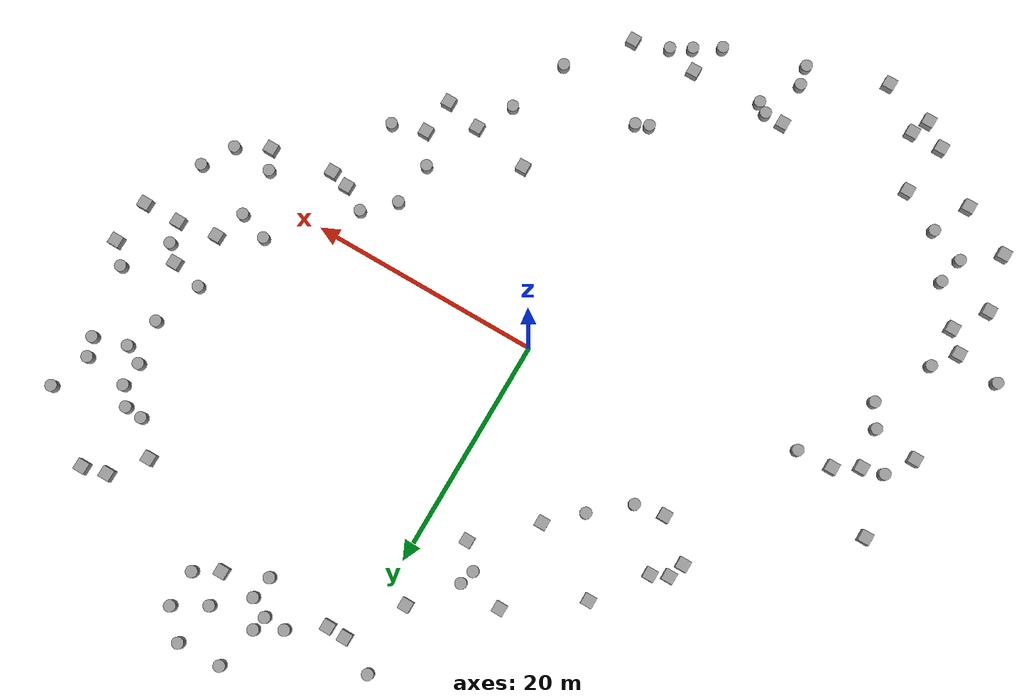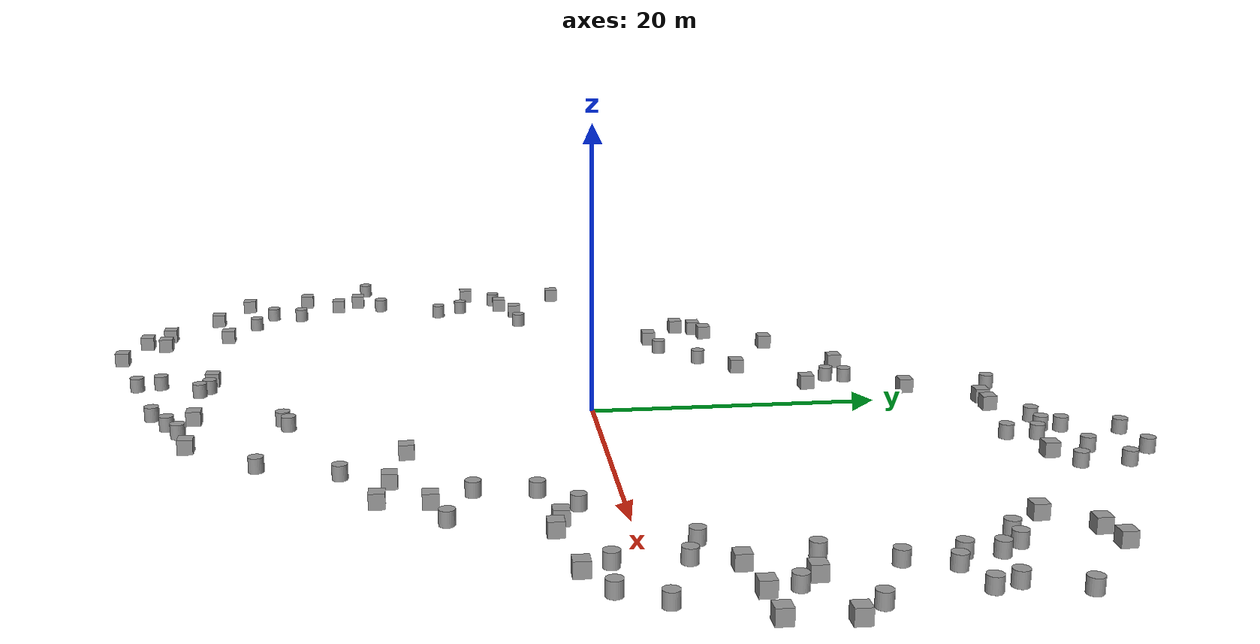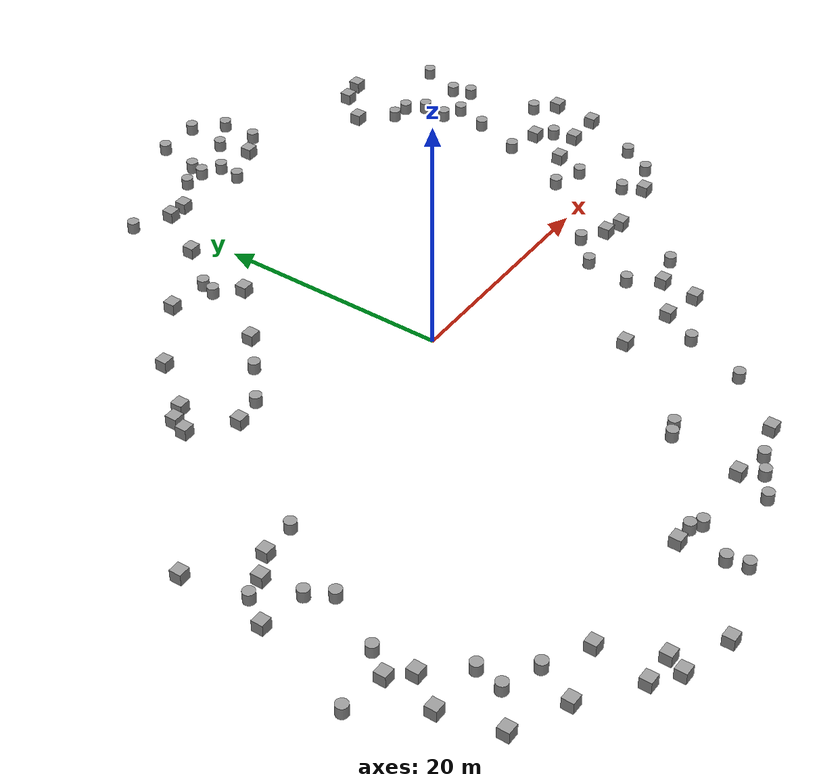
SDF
<sdf version="1.4">
 <world name="default">
  <scene>
   <sky><clouds><speed>12</speed></clouds></sky>
   <ambient>1.0 1.0 1.0 1.0</ambient>
   <shadows>false</shadows>
  </scene>
  <include><uri>model://urdf/models/sun</uri></include>
  <physics type="ode">
   <max_step_size>0.0025</max_step_size>
   <real_time_factor>0</real_time_factor>
   <real_time_update_rate>1000</real_time_update_rate>
   <gravity>0 0 -9.8</gravity>
  </physics>
  <model name="box_0">
   <pose>8.049341 -12.795973 0.500000 0.000000 0.000000 0.000000</pose>
   <link name="link">
    <inertial>
     <mass>1.000000</mass>
     <inertia>
      <ixx>0.166667</ixx>
      <ixy>0</ixy>
      <ixz>0</ixz>
      <iyy>0.166667</iyy>
      <iyz>0</iyz>
      <izz>0.166667</izz>
     </inertia>
    </inertial>
    <collision name="collision">
     <geometry><box><size>1.000000 1.000000 1.000000</size></box></geometry>
    </collision>
    <visual name="visual">
     <geometry><box><size>1.000000 1.000000 1.000000</size></box></geometry>
     <material>
      <script><name>Gazebo/Grey</name><uri>file://media/materials/scripts/gazebo.material</uri></script>
     </material>
    </visual>
   </link>
  </model>
  <model name="box_1">
   <pose>-17.665519 10.951884 0.500000 0.000000 0.000000 0.000000</pose>
   <link name="link">
    <inertial>
     <mass>1.000000</mass>
     <inertia>
      <ixx>0.166667</ixx>
      <ixy>0</ixy>
      <ixz>0</ixz>
      <iyy>0.166667</iyy>
      <iyz>0</iyz>
      <izz>0.166667</izz>
     </inertia>
    </inertial>
    <collision name="collision">
     <geometry><box><size>1.000000 1.000000 1.000000</size></box></geometry>
    </collision>
    <visual name="visual">
     <geometry><box><size>1.000000 1.000000 1.000000</size></box></geometry>
     <material>
      <script><name>Gazebo/Grey</name><uri>file://media/materials/scripts/gazebo.material</uri></script>
     </material>
    </visual>
   </link>
  </model>
  <model name="cylindar_2">
   <pose>-5.322258 17.909746 0.500000 0.000000 0.000000 0.000000</pose>
   <link name="link">
    <inertial>
     <mass>1.000000</mass>
     <inertia><ixx>0.145833</ixx><ixy>0</ixy><ixz>0</ixz><iyy>0.145833</iyy><iyz>0</iyz><izz>0.125</izz></inertia>
    </inertial>
    <collision name="collision">
     <geometry><cylinder><radius>0.500000</radius><length>1.000000</length></cylinder></geometry>
    </collision>
    <visual name="visual">
     <geometry><cylinder><radius>0.500000</radius><length>1.000000</length></cylinder></geometry>
     <material>
      <script><name>Gazebo/Grey</name><uri>file://media/materials/scripts/gazebo.material</uri></script>
     </material>
    </visual>
   </link>
  </model>
  <model name="cylindar_3">
   <pose>-23.021515 -3.703456 0.500000 0.000000 0.000000 0.000000</pose>
   <link name="link">
    <inertial>
     <mass>1.000000</mass>
     <inertia><ixx>0.145833</ixx><ixy>0</ixy><ixz>0</ixz><iyy>0.145833</iyy><iyz>0</iyz><izz>0.125</izz></inertia>
    </inertial>
    <collision name="collision">
     <geometry><cylinder><radius>0.500000</radius><length>1.000000</length></cylinder></geometry>
    </collision>
    <visual name="visual">
     <geometry><cylinder><radius>0.500000</radius><length>1.000000</length></cylinder></geometry>
     <material>
      <script><name>Gazebo/Grey</name><uri>file://media/materials/scripts/gazebo.material</uri></script>
     </material>
    </visual>
   </link>
  </model>
  <model name="cylindar_4">
   <pose>12.043559 34.589456 0.500000 0.000000 0.000000 0.000000</pose>
   <link name="link">
    <inertial>
     <mass>1.000000</mass>
     <inertia><ixx>0.145833</ixx><ixy>0</ixy><ixz>0</ixz><iyy>0.145833</iyy><iyz>0</iyz><izz>0.125</izz></inertia>
    </inertial>
    <collision name="collision">
     <geometry><cylinder><radius>0.500000</radius><length>1.000000</length></cylinder></geometry>
    </collision>
    <visual name="visual">
     <geometry><cylinder><radius>0.500000</radius><length>1.000000</length></cylinder></geometry>
     <material>
      <script><name>Gazebo/Grey</name><uri>file://media/materials/scripts/gazebo.material</uri></script>
     </material>
    </visual>
   </link>
  </model>
  <model name="cylindar_5">
   <pose>-1.222128 -30.100586 0.500000 0.000000 0.000000 0.000000</pose>
   <link name="link">
    <inertial>
     <mass>1.000000</mass>
     <inertia><ixx>0.145833</ixx><ixy>0</ixy><ixz>0</ixz><iyy>0.145833</iyy><iyz>0</iyz><izz>0.125</izz></inertia>
    </inertial>
    <collision name="collision">
     <geometry><cylinder><radius>0.500000</radius><length>1.000000</length></cylinder></geometry>
    </collision>
    <visual name="visual">
     <geometry><cylinder><radius>0.500000</radius><length>1.000000</length></cylinder></geometry>
     <material>
      <script><name>Gazebo/Grey</name><uri>file://media/materials/scripts/gazebo.material</uri></script>
     </material>
    </visual>
   </link>
  </model>
  <model name="box_6">
   <pose>16.189619 -14.473854 0.500000 0.000000 0.000000 0.000000</pose>
   <link name="link">
    <inertial>
     <mass>1.000000</mass>
     <inertia>
      <ixx>0.166667</ixx>
      <ixy>0</ixy>
      <ixz>0</ixz>
      <iyy>0.166667</iyy>
      <iyz>0</iyz>
      <izz>0.166667</izz>
     </inertia>
    </inertial>
    <collision name="collision">
     <geometry><box><size>1.000000 1.000000 1.000000</size></box></geometry>
    </collision>
    <visual name="visual">
     <geometry><box><size>1.000000 1.000000 1.000000</size></box></geometry>
     <material>
      <script><name>Gazebo/Grey</name><uri>file://media/materials/scripts/gazebo.material</uri></script>
     </material>
    </visual>
   </link>
  </model>
  <model name="box_7">
   <pose>-31.569932 -7.850897 0.500000 0.000000 0.000000 0.000000</pose>
   <link name="link">
    <inertial>
     <mass>1.000000</mass>
     <inertia>
      <ixx>0.166667</ixx>
      <ixy>0</ixy>
      <ixz>0</ixz>
      <iyy>0.166667</iyy>
      <iyz>0</iyz>
      <izz>0.166667</izz>
     </inertia>
    </inertial>
    <collision name="collision">
     <geometry><box><size>1.000000 1.000000 1.000000</size></box></geometry>
    </collision>
    <visual name="visual">
     <geometry><box><size>1.000000 1.000000 1.000000</size></box></geometry>
     <material>
      <script><name>Gazebo/Grey</name><uri>file://media/materials/scripts/gazebo.material</uri></script>
     </material>
    </visual>
   </link>
  </model>
  <model name="cylindar_8">
   <pose>0.912190 -28.786770 0.500000 0.000000 0.000000 0.000000</pose>
   <link name="link">
    <inertial>
     <mass>1.000000</mass>
     <inertia><ixx>0.145833</ixx><ixy>0</ixy><ixz>0</ixz><iyy>0.145833</iyy><iyz>0</iyz><izz>0.125</izz></inertia>
    </inertial>
    <collision name="collision">
     <geometry><cylinder><radius>0.500000</radius><length>1.000000</length></cylinder></geometry>
    </collision>
    <visual name="visual">
     <geometry><cylinder><radius>0.500000</radius><length>1.000000</length></cylinder></geometry>
     <material>
      <script><name>Gazebo/Grey</name><uri>file://media/materials/scripts/gazebo.material</uri></script>
     </material>
    </visual>
   </link>
  </model>
  <model name="cylindar_9">
   <pose>-7.065513 -26.953023 0.500000 0.000000 0.000000 0.000000</pose>
   <link name="link">
    <inertial>
     <mass>1.000000</mass>
     <inertia><ixx>0.145833</ixx><ixy>0</ixy><ixz>0</ixz><iyy>0.145833</iyy><iyz>0</iyz><izz>0.125</izz></inertia>
    </inertial>
    <collision name="collision">
     <geometry><cylinder><radius>0.500000</radius><length>1.000000</length></cylinder></geometry>
    </collision>
    <visual name="visual">
     <geometry><cylinder><radius>0.500000</radius><length>1.000000</length></cylinder></geometry>
     <material>
      <script><name>Gazebo/Grey</name><uri>file://media/materials/scripts/gazebo.material</uri></script>
     </material>
    </visual>
   </link>
  </model>
  <model name="box_10">
   <pose>-31.115598 -0.322623 0.500000 0.000000 0.000000 0.000000</pose>
   <link name="link">
    <inertial>
     <mass>1.000000</mass>
     <inertia>
      <ixx>0.166667</ixx>
      <ixy>0</ixy>
      <ixz>0</ixz>
      <iyy>0.166667</iyy>
      <iyz>0</iyz>
      <izz>0.166667</izz>
     </inertia>
    </inertial>
    <collision name="collision">
     <geometry><box><size>1.000000 1.000000 1.000000</size></box></geometry>
    </collision>
    <visual name="visual">
     <geometry><box><size>1.000000 1.000000 1.000000</size></box></geometry>
     <material>
      <script><name>Gazebo/Grey</name><uri>file://media/materials/scripts/gazebo.material</uri></script>
     </material>
    </visual>
   </link>
  </model>
  <model name="box_11">
   <pose>-2.035579 22.907309 0.500000 0.000000 0.000000 0.000000</pose>
   <link name="link">
    <inertial>
     <mass>1.000000</mass>
     <inertia>
      <ixx>0.166667</ixx>
      <ixy>0</ixy>
      <ixz>0</ixz>
      <iyy>0.166667</iyy>
      <iyz>0</iyz>
      <izz>0.166667</izz>
     </inertia>
    </inertial>
    <collision name="collision">
     <geometry><box><size>1.000000 1.000000 1.000000</size></box></geometry>
    </collision>
    <visual name="visual">
     <geometry><box><size>1.000000 1.000000 1.000000</size></box></geometry>
     <material>
      <script><name>Gazebo/Grey</name><uri>file://media/materials/scripts/gazebo.material</uri></script>
     </material>
    </visual>
   </link>
  </model>
  <model name="box_12">
   <pose>-0.121073 -27.125855 0.500000 0.000000 0.000000 0.000000</pose>
   <link name="link">
    <inertial>
     <mass>1.000000</mass>
     <inertia>
      <ixx>0.166667</ixx>
      <ixy>0</ixy>
      <ixz>0</ixz>
      <iyy>0.166667</iyy>
      <iyz>0</iyz>
      <izz>0.166667</izz>
     </inertia>
    </inertial>
    <collision name="collision">
     <geometry><box><size>1.000000 1.000000 1.000000</size></box></geometry>
    </collision>
    <visual name="visual">
     <geometry><box><size>1.000000 1.000000 1.000000</size></box></geometry>
     <material>
      <script><name>Gazebo/Grey</name><uri>file://media/materials/scripts/gazebo.material</uri></script>
     </material>
    </visual>
   </link>
  </model>
  <model name="cylindar_13">
   <pose>14.152731 32.445312 0.500000 0.000000 0.000000 0.000000</pose>
   <link name="link">
    <inertial>
     <mass>1.000000</mass>
     <inertia><ixx>0.145833</ixx><ixy>0</ixy><ixz>0</ixz><iyy>0.145833</iyy><iyz>0</iyz><izz>0.125</izz></inertia>
    </inertial>
    <collision name="collision">
     <geometry><cylinder><radius>0.500000</radius><length>1.000000</length></cylinder></geometry>
    </collision>
    <visual name="visual">
     <geometry><cylinder><radius>0.500000</radius><length>1.000000</length></cylinder></geometry>
     <material>
      <script><name>Gazebo/Grey</name><uri>file://media/materials/scripts/gazebo.material</uri></script>
     </material>
    </visual>
   </link>
  </model>
  <model name="cylindar_14">
   <pose>1.834610 -20.665780 0.500000 0.000000 0.000000 0.000000</pose>
   <link name="link">
    <inertial>
     <mass>1.000000</mass>
     <inertia><ixx>0.145833</ixx><ixy>0</ixy><ixz>0</ixz><iyy>0.145833</iyy><iyz>0</iyz><izz>0.125</izz></inertia>
    </inertial>
    <collision name="collision">
     <geometry><cylinder><radius>0.500000</radius><length>1.000000</length></cylinder></geometry>
    </collision>
    <visual name="visual">
     <geometry><cylinder><radius>0.500000</radius><length>1.000000</length></cylinder></geometry>
     <material>
      <script><name>Gazebo/Grey</name><uri>file://media/materials/scripts/gazebo.material</uri></script>
     </material>
    </visual>
   </link>
  </model>
  <model name="cylindar_15">
   <pose>25.929253 9.365145 0.500000 0.000000 0.000000 0.000000</pose>
   <link name="link">
    <inertial>
     <mass>1.000000</mass>
     <inertia><ixx>0.145833</ixx><ixy>0</ixy><ixz>0</ixz><iyy>0.145833</iyy><iyz>0</iyz><izz>0.125</izz></inertia>
    </inertial>
    <collision name="collision">
     <geometry><cylinder><radius>0.500000</radius><length>1.000000</length></cylinder></geometry>
    </collision>
    <visual name="visual">
     <geometry><cylinder><radius>0.500000</radius><length>1.000000</length></cylinder></geometry>
     <material>
      <script><name>Gazebo/Grey</name><uri>file://media/materials/scripts/gazebo.material</uri></script>
     </material>
    </visual>
   </link>
  </model>
  <model name="cylindar_16">
   <pose>29.565730 -2.149706 0.500000 0.000000 0.000000 0.000000</pose>
   <link name="link">
    <inertial>
     <mass>1.000000</mass>
     <inertia><ixx>0.145833</ixx><ixy>0</ixy><ixz>0</ixz><iyy>0.145833</iyy><iyz>0</iyz><izz>0.125</izz></inertia>
    </inertial>
    <collision name="collision">
     <geometry><cylinder><radius>0.500000</radius><length>1.000000</length></cylinder></geometry>
    </collision>
    <visual name="visual">
     <geometry><cylinder><radius>0.500000</radius><length>1.000000</length></cylinder></geometry>
     <material>
      <script><name>Gazebo/Grey</name><uri>file://media/materials/scripts/gazebo.material</uri></script>
     </material>
    </visual>
   </link>
  </model>
  <model name="box_17">
   <pose>-16.359451 6.270912 0.500000 0.000000 0.000000 0.000000</pose>
   <link name="link">
    <inertial>
     <mass>1.000000</mass>
     <inertia>
      <ixx>0.166667</ixx>
      <ixy>0</ixy>
      <ixz>0</ixz>
      <iyy>0.166667</iyy>
      <iyz>0</iyz>
      <izz>0.166667</izz>
     </inertia>
    </inertial>
    <collision name="collision">
     <geometry><box><size>1.000000 1.000000 1.000000</size></box></geometry>
    </collision>
    <visual name="visual">
     <geometry><box><size>1.000000 1.000000 1.000000</size></box></geometry>
     <material>
      <script><name>Gazebo/Grey</name><uri>file://media/materials/scripts/gazebo.material</uri></script>
     </material>
    </visual>
   </link>
  </model>
  <model name="cylindar_18">
   <pose>19.340142 -10.447154 0.500000 0.000000 0.000000 0.000000</pose>
   <link name="link">
    <inertial>
     <mass>1.000000</mass>
     <inertia><ixx>0.145833</ixx><ixy>0</ixy><ixz>0</ixz><iyy>0.145833</iyy><iyz>0</iyz><izz>0.125</izz></inertia>
    </inertial>
    <collision name="collision">
     <geometry><cylinder><radius>0.500000</radius><length>1.000000</length></cylinder></geometry>
    </collision>
    <visual name="visual">
     <geometry><cylinder><radius>0.500000</radius><length>1.000000</length></cylinder></geometry>
     <material>
      <script><name>Gazebo/Grey</name><uri>file://media/materials/scripts/gazebo.material</uri></script>
     </material>
    </visual>
   </link>
  </model>
  <model name="box_19">
   <pose>-20.448026 -27.128200 0.500000 0.000000 0.000000 0.000000</pose>
   <link name="link">
    <inertial>
     <mass>1.000000</mass>
     <inertia>
      <ixx>0.166667</ixx>
      <ixy>0</ixy>
      <ixz>0</ixz>
      <iyy>0.166667</iyy>
      <iyz>0</iyz>
      <izz>0.166667</izz>
     </inertia>
    </inertial>
    <collision name="collision">
     <geometry><box><size>1.000000 1.000000 1.000000</size></box></geometry>
    </collision>
    <visual name="visual">
     <geometry><box><size>1.000000 1.000000 1.000000</size></box></geometry>
     <material>
      <script><name>Gazebo/Grey</name><uri>file://media/materials/scripts/gazebo.material</uri></script>
     </material>
    </visual>
   </link>
  </model>
  <model name="box_20">
   <pose>-21.140862 -31.742281 0.500000 0.000000 0.000000 0.000000</pose>
   <link name="link">
    <inertial>
     <mass>1.000000</mass>
     <inertia>
      <ixx>0.166667</ixx>
      <ixy>0</ixy>
      <ixz>0</ixz>
      <iyy>0.166667</iyy>
      <iyz>0</iyz>
      <izz>0.166667</izz>
     </inertia>
    </inertial>
    <collision name="collision">
     <geometry><box><size>1.000000 1.000000 1.000000</size></box></geometry>
    </collision>
    <visual name="visual">
     <geometry><box><size>1.000000 1.000000 1.000000</size></box></geometry>
     <material>
      <script><name>Gazebo/Grey</name><uri>file://media/materials/scripts/gazebo.material</uri></script>
     </material>
    </visual>
   </link>
  </model>
  <model name="box_21">
   <pose>12.042444 28.069900 0.500000 0.000000 0.000000 0.000000</pose>
   <link name="link">
    <inertial>
     <mass>1.000000</mass>
     <inertia>
      <ixx>0.166667</ixx>
      <ixy>0</ixy>
      <ixz>0</ixz>
      <iyy>0.166667</iyy>
      <iyz>0</iyz>
      <izz>0.166667</izz>
     </inertia>
    </inertial>
    <collision name="collision">
     <geometry><box><size>1.000000 1.000000 1.000000</size></box></geometry>
    </collision>
    <visual name="visual">
     <geometry><box><size>1.000000 1.000000 1.000000</size></box></geometry>
     <material>
      <script><name>Gazebo/Grey</name><uri>file://media/materials/scripts/gazebo.material</uri></script>
     </material>
    </visual>
   </link>
  </model>
  <model name="cylindar_22">
   <pose>26.872980 19.345198 0.500000 0.000000 0.000000 0.000000</pose>
   <link name="link">
    <inertial>
     <mass>1.000000</mass>
     <inertia><ixx>0.145833</ixx><ixy>0</ixy><ixz>0</ixz><iyy>0.145833</iyy><iyz>0</iyz><izz>0.125</izz></inertia>
    </inertial>
    <collision name="collision">
     <geometry><cylinder><radius>0.500000</radius><length>1.000000</length></cylinder></geometry>
    </collision>
    <visual name="visual">
     <geometry><cylinder><radius>0.500000</radius><length>1.000000</length></cylinder></geometry>
     <material>
      <script><name>Gazebo/Grey</name><uri>file://media/materials/scripts/gazebo.material</uri></script>
     </material>
    </visual>
   </link>
  </model>
  <model name="cylindar_23">
   <pose>-8.398775 -30.569420 0.500000 0.000000 0.000000 0.000000</pose>
   <link name="link">
    <inertial>
     <mass>1.000000</mass>
     <inertia><ixx>0.145833</ixx><ixy>0</ixy><ixz>0</ixz><iyy>0.145833</iyy><iyz>0</iyz><izz>0.125</izz></inertia>
    </inertial>
    <collision name="collision">
     <geometry><cylinder><radius>0.500000</radius><length>1.000000</length></cylinder></geometry>
    </collision>
    <visual name="visual">
     <geometry><cylinder><radius>0.500000</radius><length>1.000000</length></cylinder></geometry>
     <material>
      <script><name>Gazebo/Grey</name><uri>file://media/materials/scripts/gazebo.material</uri></script>
     </material>
    </visual>
   </link>
  </model>
  <model name="cylindar_24">
   <pose>-2.232297 29.077389 0.500000 0.000000 0.000000 0.000000</pose>
   <link name="link">
    <inertial>
     <mass>1.000000</mass>
     <inertia><ixx>0.145833</ixx><ixy>0</ixy><ixz>0</ixz><iyy>0.145833</iyy><iyz>0</iyz><izz>0.125</izz></inertia>
    </inertial>
    <collision name="collision">
     <geometry><cylinder><radius>0.500000</radius><length>1.000000</length></cylinder></geometry>
    </collision>
    <visual name="visual">
     <geometry><cylinder><radius>0.500000</radius><length>1.000000</length></cylinder></geometry>
     <material>
      <script><name>Gazebo/Grey</name><uri>file://media/materials/scripts/gazebo.material</uri></script>
     </material>
    </visual>
   </link>
  </model>
  <model name="box_25">
   <pose>26.909636 4.998011 0.500000 0.000000 0.000000 0.000000</pose>
   <link name="link">
    <inertial>
     <mass>1.000000</mass>
     <inertia>
      <ixx>0.166667</ixx>
      <ixy>0</ixy>
      <ixz>0</ixz>
      <iyy>0.166667</iyy>
      <iyz>0</iyz>
      <izz>0.166667</izz>
     </inertia>
    </inertial>
    <collision name="collision">
     <geometry><box><size>1.000000 1.000000 1.000000</size></box></geometry>
    </collision>
    <visual name="visual">
     <geometry><box><size>1.000000 1.000000 1.000000</size></box></geometry>
     <material>
      <script><name>Gazebo/Grey</name><uri>file://media/materials/scripts/gazebo.material</uri></script>
     </material>
    </visual>
   </link>
  </model>
  <model name="cylindar_26">
   <pose>29.852892 7.454227 0.500000 0.000000 0.000000 0.000000</pose>
   <link name="link">
    <inertial>
     <mass>1.000000</mass>
     <inertia><ixx>0.145833</ixx><ixy>0</ixy><ixz>0</ixz><iyy>0.145833</iyy><iyz>0</iyz><izz>0.125</izz></inertia>
    </inertial>
    <collision name="collision">
     <geometry><cylinder><radius>0.500000</radius><length>1.000000</length></cylinder></geometry>
    </collision>
    <visual name="visual">
     <geometry><cylinder><radius>0.500000</radius><length>1.000000</length></cylinder></geometry>
     <material>
      <script><name>Gazebo/Grey</name><uri>file://media/materials/scripts/gazebo.material</uri></script>
     </material>
    </visual>
   </link>
  </model>
  <model name="cylindar_27">
   <pose>-4.958954 19.207233 0.500000 0.000000 0.000000 0.000000</pose>
   <link name="link">
    <inertial>
     <mass>1.000000</mass>
     <inertia><ixx>0.145833</ixx><ixy>0</ixy><ixz>0</ixz><iyy>0.145833</iyy><iyz>0</iyz><izz>0.125</izz></inertia>
    </inertial>
    <collision name="collision">
     <geometry><cylinder><radius>0.500000</radius><length>1.000000</length></cylinder></geometry>
    </collision>
    <visual name="visual">
     <geometry><cylinder><radius>0.500000</radius><length>1.000000</length></cylinder></geometry>
     <material>
      <script><name>Gazebo/Grey</name><uri>file://media/materials/scripts/gazebo.material</uri></script>
     </material>
    </visual>
   </link>
  </model>
  <model name="cylindar_28">
   <pose>31.890558 22.335854 0.500000 0.000000 0.000000 0.000000</pose>
   <link name="link">
    <inertial>
     <mass>1.000000</mass>
     <inertia><ixx>0.145833</ixx><ixy>0</ixy><ixz>0</ixz><iyy>0.145833</iyy><iyz>0</iyz><izz>0.125</izz></inertia>
    </inertial>
    <collision name="collision">
     <geometry><cylinder><radius>0.500000</radius><length>1.000000</length></cylinder></geometry>
    </collision>
    <visual name="visual">
     <geometry><cylinder><radius>0.500000</radius><length>1.000000</length></cylinder></geometry>
     <material>
      <script><name>Gazebo/Grey</name><uri>file://media/materials/scripts/gazebo.material</uri></script>
     </material>
    </visual>
   </link>
  </model>
  <model name="box_29">
   <pose>-26.080019 -3.890634 0.500000 0.000000 0.000000 0.000000</pose>
   <link name="link">
    <inertial>
     <mass>1.000000</mass>
     <inertia>
      <ixx>0.166667</ixx>
      <ixy>0</ixy>
      <ixz>0</ixz>
      <iyy>0.166667</iyy>
      <iyz>0</iyz>
      <izz>0.166667</izz>
     </inertia>
    </inertial>
    <collision name="collision">
     <geometry><box><size>1.000000 1.000000 1.000000</size></box></geometry>
    </collision>
    <visual name="visual">
     <geometry><box><size>1.000000 1.000000 1.000000</size></box></geometry>
     <material>
      <script><name>Gazebo/Grey</name><uri>file://media/materials/scripts/gazebo.material</uri></script>
     </material>
    </visual>
   </link>
  </model>
  <model name="cylindar_30">
   <pose>14.987610 -8.820955 0.500000 0.000000 0.000000 0.000000</pose>
   <link name="link">
    <inertial>
     <mass>1.000000</mass>
     <inertia><ixx>0.145833</ixx><ixy>0</ixy><ixz>0</ixz><iyy>0.145833</iyy><iyz>0</iyz><izz>0.125</izz></inertia>
    </inertial>
    <collision name="collision">
     <geometry><cylinder><radius>0.500000</radius><length>1.000000</length></cylinder></geometry>
    </collision>
    <visual name="visual">
     <geometry><cylinder><radius>0.500000</radius><length>1.000000</length></cylinder></geometry>
     <material>
      <script><name>Gazebo/Grey</name><uri>file://media/materials/scripts/gazebo.material</uri></script>
     </material>
    </visual>
   </link>
  </model>
  <model name="cylindar_31">
   <pose>-8.042111 -32.215314 0.500000 0.000000 0.000000 0.000000</pose>
   <link name="link">
    <inertial>
     <mass>1.000000</mass>
     <inertia><ixx>0.145833</ixx><ixy>0</ixy><ixz>0</ixz><iyy>0.145833</iyy><iyz>0</iyz><izz>0.125</izz></inertia>
    </inertial>
    <collision name="collision">
     <geometry><cylinder><radius>0.500000</radius><length>1.000000</length></cylinder></geometry>
    </collision>
    <visual name="visual">
     <geometry><cylinder><radius>0.500000</radius><length>1.000000</length></cylinder></geometry>
     <material>
      <script><name>Gazebo/Grey</name><uri>file://media/materials/scripts/gazebo.material</uri></script>
     </material>
    </visual>
   </link>
  </model>
  <model name="box_32">
   <pose>24.177609 26.104941 0.500000 0.000000 0.000000 0.000000</pose>
   <link name="link">
    <inertial>
     <mass>1.000000</mass>
     <inertia>
      <ixx>0.166667</ixx>
      <ixy>0</ixy>
      <ixz>0</ixz>
      <iyy>0.166667</iyy>
      <iyz>0</iyz>
      <izz>0.166667</izz>
     </inertia>
    </inertial>
    <collision name="collision">
     <geometry><box><size>1.000000 1.000000 1.000000</size></box></geometry>
    </collision>
    <visual name="visual">
     <geometry><box><size>1.000000 1.000000 1.000000</size></box></geometry>
     <material>
      <script><name>Gazebo/Grey</name><uri>file://media/materials/scripts/gazebo.material</uri></script>
     </material>
    </visual>
   </link>
  </model>
  <model name="cylindar_33">
   <pose>15.416123 -5.012400 0.500000 0.000000 0.000000 0.000000</pose>
   <link name="link">
    <inertial>
     <mass>1.000000</mass>
     <inertia><ixx>0.145833</ixx><ixy>0</ixy><ixz>0</ixz><iyy>0.145833</iyy><iyz>0</iyz><izz>0.125</izz></inertia>
    </inertial>
    <collision name="collision">
     <geometry><cylinder><radius>0.500000</radius><length>1.000000</length></cylinder></geometry>
    </collision>
    <visual name="visual">
     <geometry><cylinder><radius>0.500000</radius><length>1.000000</length></cylinder></geometry>
     <material>
      <script><name>Gazebo/Grey</name><uri>file://media/materials/scripts/gazebo.material</uri></script>
     </material>
    </visual>
   </link>
  </model>
  <model name="box_34">
   <pose>33.836100 9.510949 0.500000 0.000000 0.000000 0.000000</pose>
   <link name="link">
    <inertial>
     <mass>1.000000</mass>
     <inertia>
      <ixx>0.166667</ixx>
      <ixy>0</ixy>
      <ixz>0</ixz>
      <iyy>0.166667</iyy>
      <iyz>0</iyz>
      <izz>0.166667</izz>
     </inertia>
    </inertial>
    <collision name="collision">
     <geometry><box><size>1.000000 1.000000 1.000000</size></box></geometry>
    </collision>
    <visual name="visual">
     <geometry><box><size>1.000000 1.000000 1.000000</size></box></geometry>
     <material>
      <script><name>Gazebo/Grey</name><uri>file://media/materials/scripts/gazebo.material</uri></script>
     </material>
    </visual>
   </link>
  </model>
  <model name="cylindar_35">
   <pose>-29.066448 -15.208298 0.500000 0.000000 0.000000 0.000000</pose>
   <link name="link">
    <inertial>
     <mass>1.000000</mass>
     <inertia><ixx>0.145833</ixx><ixy>0</ixy><ixz>0</ixz><iyy>0.145833</iyy><iyz>0</iyz><izz>0.125</izz></inertia>
    </inertial>
    <collision name="collision">
     <geometry><cylinder><radius>0.500000</radius><length>1.000000</length></cylinder></geometry>
    </collision>
    <visual name="visual">
     <geometry><cylinder><radius>0.500000</radius><length>1.000000</length></cylinder></geometry>
     <material>
      <script><name>Gazebo/Grey</name><uri>file://media/materials/scripts/gazebo.material</uri></script>
     </material>
    </visual>
   </link>
  </model>
  <model name="cylindar_36">
   <pose>9.520125 -22.059783 0.500000 0.000000 0.000000 0.000000</pose>
   <link name="link">
    <inertial>
     <mass>1.000000</mass>
     <inertia><ixx>0.145833</ixx><ixy>0</ixy><ixz>0</ixz><iyy>0.145833</iyy><iyz>0</iyz><izz>0.125</izz></inertia>
    </inertial>
    <collision name="collision">
     <geometry><cylinder><radius>0.500000</radius><length>1.000000</length></cylinder></geometry>
    </collision>
    <visual name="visual">
     <geometry><cylinder><radius>0.500000</radius><length>1.000000</length></cylinder></geometry>
     <material>
      <script><name>Gazebo/Grey</name><uri>file://media/materials/scripts/gazebo.material</uri></script>
     </material>
    </visual>
   </link>
  </model>
  <model name="cylindar_37">
   <pose>-26.492907 -21.793048 0.500000 0.000000 0.000000 0.000000</pose>
   <link name="link">
    <inertial>
     <mass>1.000000</mass>
     <inertia><ixx>0.145833</ixx><ixy>0</ixy><ixz>0</ixz><iyy>0.145833</iyy><iyz>0</iyz><izz>0.125</izz></inertia>
    </inertial>
    <collision name="collision">
     <geometry><cylinder><radius>0.500000</radius><length>1.000000</length></cylinder></geometry>
    </collision>
    <visual name="visual">
     <geometry><cylinder><radius>0.500000</radius><length>1.000000</length></cylinder></geometry>
     <material>
      <script><name>Gazebo/Grey</name><uri>file://media/materials/scripts/gazebo.material</uri></script>
     </material>
    </visual>
   </link>
  </model>
  <model name="box_38">
   <pose>-3.653764 16.031023 0.500000 0.000000 0.000000 0.000000</pose>
   <link name="link">
    <inertial>
     <mass>1.000000</mass>
     <inertia>
      <ixx>0.166667</ixx>
      <ixy>0</ixy>
      <ixz>0</ixz>
      <iyy>0.166667</iyy>
      <iyz>0</iyz>
      <izz>0.166667</izz>
     </inertia>
    </inertial>
    <collision name="collision">
     <geometry><box><size>1.000000 1.000000 1.000000</size></box></geometry>
    </collision>
    <visual name="visual">
     <geometry><box><size>1.000000 1.000000 1.000000</size></box></geometry>
     <material>
      <script><name>Gazebo/Grey</name><uri>file://media/materials/scripts/gazebo.material</uri></script>
     </material>
    </visual>
   </link>
  </model>
  <model name="box_39">
   <pose>13.050045 -13.792314 0.500000 0.000000 0.000000 0.000000</pose>
   <link name="link">
    <inertial>
     <mass>1.000000</mass>
     <inertia>
      <ixx>0.166667</ixx>
      <ixy>0</ixy>
      <ixz>0</ixz>
      <iyy>0.166667</iyy>
      <iyz>0</iyz>
      <izz>0.166667</izz>
     </inertia>
    </inertial>
    <collision name="collision">
     <geometry><box><size>1.000000 1.000000 1.000000</size></box></geometry>
    </collision>
    <visual name="visual">
     <geometry><box><size>1.000000 1.000000 1.000000</size></box></geometry>
     <material>
      <script><name>Gazebo/Grey</name><uri>file://media/materials/scripts/gazebo.material</uri></script>
     </material>
    </visual>
   </link>
  </model>
  <model name="box_40">
   <pose>-19.147465 -33.238386 0.500000 0.000000 0.000000 0.000000</pose>
   <link name="link">
    <inertial>
     <mass>1.000000</mass>
     <inertia>
      <ixx>0.166667</ixx>
      <ixy>0</ixy>
      <ixz>0</ixz>
      <iyy>0.166667</iyy>
      <iyz>0</iyz>
      <izz>0.166667</izz>
     </inertia>
    </inertial>
    <collision name="collision">
     <geometry><box><size>1.000000 1.000000 1.000000</size></box></geometry>
    </collision>
    <visual name="visual">
     <geometry><box><size>1.000000 1.000000 1.000000</size></box></geometry>
     <material>
      <script><name>Gazebo/Grey</name><uri>file://media/materials/scripts/gazebo.material</uri></script>
     </material>
    </visual>
   </link>
  </model>
  <model name="cylindar_41">
   <pose>11.443076 30.857965 0.500000 0.000000 0.000000 0.000000</pose>
   <link name="link">
    <inertial>
     <mass>1.000000</mass>
     <inertia><ixx>0.145833</ixx><ixy>0</ixy><ixz>0</ixz><iyy>0.145833</iyy><iyz>0</iyz><izz>0.125</izz></inertia>
    </inertial>
    <collision name="collision">
     <geometry><cylinder><radius>0.500000</radius><length>1.000000</length></cylinder></geometry>
    </collision>
    <visual name="visual">
     <geometry><cylinder><radius>0.500000</radius><length>1.000000</length></cylinder></geometry>
     <material>
      <script><name>Gazebo/Grey</name><uri>file://media/materials/scripts/gazebo.material</uri></script>
     </material>
    </visual>
   </link>
  </model>
  <model name="box_42">
   <pose>-29.863723 -26.392566 0.500000 0.000000 0.000000 0.000000</pose>
   <link name="link">
    <inertial>
     <mass>1.000000</mass>
     <inertia>
      <ixx>0.166667</ixx>
      <ixy>0</ixy>
      <ixz>0</ixz>
      <iyy>0.166667</iyy>
      <iyz>0</iyz>
      <izz>0.166667</izz>
     </inertia>
    </inertial>
    <collision name="collision">
     <geometry><box><size>1.000000 1.000000 1.000000</size></box></geometry>
    </collision>
    <visual name="visual">
     <geometry><box><size>1.000000 1.000000 1.000000</size></box></geometry>
     <material>
      <script><name>Gazebo/Grey</name><uri>file://media/materials/scripts/gazebo.material</uri></script>
     </material>
    </visual>
   </link>
  </model>
  <model name="cylindar_43">
   <pose>-23.945715 -25.249269 0.500000 0.000000 0.000000 0.000000</pose>
   <link name="link">
    <inertial>
     <mass>1.000000</mass>
     <inertia><ixx>0.145833</ixx><ixy>0</ixy><ixz>0</ixz><iyy>0.145833</iyy><iyz>0</iyz><izz>0.125</izz></inertia>
    </inertial>
    <collision name="collision">
     <geometry><cylinder><radius>0.500000</radius><length>1.000000</length></cylinder></geometry>
    </collision>
    <visual name="visual">
     <geometry><cylinder><radius>0.500000</radius><length>1.000000</length></cylinder></geometry>
     <material>
      <script><name>Gazebo/Grey</name><uri>file://media/materials/scripts/gazebo.material</uri></script>
     </material>
    </visual>
   </link>
  </model>
  <model name="cylindar_44">
   <pose>-13.803489 6.749120 0.500000 0.000000 0.000000 0.000000</pose>
   <link name="link">
    <inertial>
     <mass>1.000000</mass>
     <inertia><ixx>0.145833</ixx><ixy>0</ixy><ixz>0</ixz><iyy>0.145833</iyy><iyz>0</iyz><izz>0.125</izz></inertia>
    </inertial>
    <collision name="collision">
     <geometry><cylinder><radius>0.500000</radius><length>1.000000</length></cylinder></geometry>
    </collision>
    <visual name="visual">
     <geometry><cylinder><radius>0.500000</radius><length>1.000000</length></cylinder></geometry>
     <material>
      <script><name>Gazebo/Grey</name><uri>file://media/materials/scripts/gazebo.material</uri></script>
     </material>
    </visual>
   </link>
  </model>
  <model name="box_45">
   <pose>-8.738110 -26.936090 0.500000 0.000000 0.000000 0.000000</pose>
   <link name="link">
    <inertial>
     <mass>1.000000</mass>
     <inertia>
      <ixx>0.166667</ixx>
      <ixy>0</ixy>
      <ixz>0</ixz>
      <iyy>0.166667</iyy>
      <iyz>0</iyz>
      <izz>0.166667</izz>
     </inertia>
    </inertial>
    <collision name="collision">
     <geometry><box><size>1.000000 1.000000 1.000000</size></box></geometry>
    </collision>
    <visual name="visual">
     <geometry><box><size>1.000000 1.000000 1.000000</size></box></geometry>
     <material>
      <script><name>Gazebo/Grey</name><uri>file://media/materials/scripts/gazebo.material</uri></script>
     </material>
    </visual>
   </link>
  </model>
  <model name="cylindar_46">
   <pose>-10.776565 9.318425 0.500000 0.000000 0.000000 0.000000</pose>
   <link name="link">
    <inertial>
     <mass>1.000000</mass>
     <inertia><ixx>0.145833</ixx><ixy>0</ixy><ixz>0</ixz><iyy>0.145833</iyy><iyz>0</iyz><izz>0.125</izz></inertia>
    </inertial>
    <collision name="collision">
     <geometry><cylinder><radius>0.500000</radius><length>1.000000</length></cylinder></geometry>
    </collision>
    <visual name="visual">
     <geometry><cylinder><radius>0.500000</radius><length>1.000000</length></cylinder></geometry>
     <material>
      <script><name>Gazebo/Grey</name><uri>file://media/materials/scripts/gazebo.material</uri></script>
     </material>
    </visual>
   </link>
  </model>
  <model name="box_47">
   <pose>19.829592 -4.010149 0.500000 0.000000 0.000000 0.000000</pose>
   <link name="link">
    <inertial>
     <mass>1.000000</mass>
     <inertia>
      <ixx>0.166667</ixx>
      <ixy>0</ixy>
      <ixz>0</ixz>
      <iyy>0.166667</iyy>
      <iyz>0</iyz>
      <izz>0.166667</izz>
     </inertia>
    </inertial>
    <collision name="collision">
     <geometry><box><size>1.000000 1.000000 1.000000</size></box></geometry>
    </collision>
    <visual name="visual">
     <geometry><box><size>1.000000 1.000000 1.000000</size></box></geometry>
     <material>
      <script><name>Gazebo/Grey</name><uri>file://media/materials/scripts/gazebo.material</uri></script>
     </material>
    </visual>
   </link>
  </model>
  <model name="cylindar_48">
   <pose>7.432728 30.696900 0.500000 0.000000 0.000000 0.000000</pose>
   <link name="link">
    <inertial>
     <mass>1.000000</mass>
     <inertia><ixx>0.145833</ixx><ixy>0</ixy><ixz>0</ixz><iyy>0.145833</iyy><iyz>0</iyz><izz>0.125</izz></inertia>
    </inertial>
    <collision name="collision">
     <geometry><cylinder><radius>0.500000</radius><length>1.000000</length></cylinder></geometry>
    </collision>
    <visual name="visual">
     <geometry><cylinder><radius>0.500000</radius><length>1.000000</length></cylinder></geometry>
     <material>
      <script><name>Gazebo/Grey</name><uri>file://media/materials/scripts/gazebo.material</uri></script>
     </material>
    </visual>
   </link>
  </model>
  <model name="cylindar_49">
   <pose>32.325318 11.130729 0.500000 0.000000 0.000000 0.000000</pose>
   <link name="link">
    <inertial>
     <mass>1.000000</mass>
     <inertia><ixx>0.145833</ixx><ixy>0</ixy><ixz>0</ixz><iyy>0.145833</iyy><iyz>0</iyz><izz>0.125</izz></inertia>
    </inertial>
    <collision name="collision">
     <geometry><cylinder><radius>0.500000</radius><length>1.000000</length></cylinder></geometry>
    </collision>
    <visual name="visual">
     <geometry><cylinder><radius>0.500000</radius><length>1.000000</length></cylinder></geometry>
     <material>
      <script><name>Gazebo/Grey</name><uri>file://media/materials/scripts/gazebo.material</uri></script>
     </material>
    </visual>
   </link>
  </model>
  <model name="box_50">
   <pose>-19.557383 8.941897 0.500000 0.000000 0.000000 0.000000</pose>
   <link name="link">
    <inertial>
     <mass>1.000000</mass>
     <inertia>
      <ixx>0.166667</ixx>
      <ixy>0</ixy>
      <ixz>0</ixz>
      <iyy>0.166667</iyy>
      <iyz>0</iyz>
      <izz>0.166667</izz>
     </inertia>
    </inertial>
    <collision name="collision">
     <geometry><box><size>1.000000 1.000000 1.000000</size></box></geometry>
    </collision>
    <visual name="visual">
     <geometry><box><size>1.000000 1.000000 1.000000</size></box></geometry>
     <material>
      <script><name>Gazebo/Grey</name><uri>file://media/materials/scripts/gazebo.material</uri></script>
     </material>
    </visual>
   </link>
  </model>
  <model name="box_51">
   <pose>-8.126249 11.760559 0.500000 0.000000 0.000000 0.000000</pose>
   <link name="link">
    <inertial>
     <mass>1.000000</mass>
     <inertia>
      <ixx>0.166667</ixx>
      <ixy>0</ixy>
      <ixz>0</ixz>
      <iyy>0.166667</iyy>
      <iyz>0</iyz>
      <izz>0.166667</izz>
     </inertia>
    </inertial>
    <collision name="collision">
     <geometry><box><size>1.000000 1.000000 1.000000</size></box></geometry>
    </collision>
    <visual name="visual">
     <geometry><box><size>1.000000 1.000000 1.000000</size></box></geometry>
     <material>
      <script><name>Gazebo/Grey</name><uri>file://media/materials/scripts/gazebo.material</uri></script>
     </material>
    </visual>
   </link>
  </model>
  <model name="box_52">
   <pose>26.225055 26.619723 0.500000 0.000000 0.000000 0.000000</pose>
   <link name="link">
    <inertial>
     <mass>1.000000</mass>
     <inertia>
      <ixx>0.166667</ixx>
      <ixy>0</ixy>
      <ixz>0</ixz>
      <iyy>0.166667</iyy>
      <iyz>0</iyz>
      <izz>0.166667</izz>
     </inertia>
    </inertial>
    <collision name="collision">
     <geometry><box><size>1.000000 1.000000 1.000000</size></box></geometry>
    </collision>
    <visual name="visual">
     <geometry><box><size>1.000000 1.000000 1.000000</size></box></geometry>
     <material>
      <script><name>Gazebo/Grey</name><uri>file://media/materials/scripts/gazebo.material</uri></script>
     </material>
    </visual>
   </link>
  </model>
  <model name="cylindar_53">
   <pose>28.302107 16.427710 0.500000 0.000000 0.000000 0.000000</pose>
   <link name="link">
    <inertial>
     <mass>1.000000</mass>
     <inertia><ixx>0.145833</ixx><ixy>0</ixy><ixz>0</ixz><iyy>0.145833</iyy><iyz>0</iyz><izz>0.125</izz></inertia>
    </inertial>
    <collision name="collision">
     <geometry><cylinder><radius>0.500000</radius><length>1.000000</length></cylinder></geometry>
    </collision>
    <visual name="visual">
     <geometry><cylinder><radius>0.500000</radius><length>1.000000</length></cylinder></geometry>
     <material>
      <script><name>Gazebo/Grey</name><uri>file://media/materials/scripts/gazebo.material</uri></script>
     </material>
    </visual>
   </link>
  </model>
  <model name="box_54">
   <pose>-25.467613 -28.480302 0.500000 0.000000 0.000000 0.000000</pose>
   <link name="link">
    <inertial>
     <mass>1.000000</mass>
     <inertia>
      <ixx>0.166667</ixx>
      <ixy>0</ixy>
      <ixz>0</ixz>
      <iyy>0.166667</iyy>
      <iyz>0</iyz>
      <izz>0.166667</izz>
     </inertia>
    </inertial>
    <collision name="collision">
     <geometry><box><size>1.000000 1.000000 1.000000</size></box></geometry>
    </collision>
    <visual name="visual">
     <geometry><box><size>1.000000 1.000000 1.000000</size></box></geometry>
     <material>
      <script><name>Gazebo/Grey</name><uri>file://media/materials/scripts/gazebo.material</uri></script>
     </material>
    </visual>
   </link>
  </model>
  <model name="cylindar_55">
   <pose>-30.006184 -5.540009 0.500000 0.000000 0.000000 0.000000</pose>
   <link name="link">
    <inertial>
     <mass>1.000000</mass>
     <inertia><ixx>0.145833</ixx><ixy>0</ixy><ixz>0</ixz><iyy>0.145833</iyy><iyz>0</iyz><izz>0.125</izz></inertia>
    </inertial>
    <collision name="collision">
     <geometry><cylinder><radius>0.500000</radius><length>1.000000</length></cylinder></geometry>
    </collision>
    <visual name="visual">
     <geometry><cylinder><radius>0.500000</radius><length>1.000000</length></cylinder></geometry>
     <material>
      <script><name>Gazebo/Grey</name><uri>file://media/materials/scripts/gazebo.material</uri></script>
     </material>
    </visual>
   </link>
  </model>
  <model name="cylindar_56">
   <pose>24.197257 20.876116 0.500000 0.000000 0.000000 0.000000</pose>
   <link name="link">
    <inertial>
     <mass>1.000000</mass>
     <inertia><ixx>0.145833</ixx><ixy>0</ixy><ixz>0</ixz><iyy>0.145833</iyy><iyz>0</iyz><izz>0.125</izz></inertia>
    </inertial>
    <collision name="collision">
     <geometry><cylinder><radius>0.500000</radius><length>1.000000</length></cylinder></geometry>
    </collision>
    <visual name="visual">
     <geometry><cylinder><radius>0.500000</radius><length>1.000000</length></cylinder></geometry>
     <material>
      <script><name>Gazebo/Grey</name><uri>file://media/materials/scripts/gazebo.material</uri></script>
     </material>
    </visual>
   </link>
  </model>
  <model name="cylindar_57">
   <pose>26.031230 -1.877455 0.500000 0.000000 0.000000 0.000000</pose>
   <link name="link">
    <inertial>
     <mass>1.000000</mass>
     <inertia><ixx>0.145833</ixx><ixy>0</ixy><ixz>0</ixz><iyy>0.145833</iyy><iyz>0</iyz><izz>0.125</izz></inertia>
    </inertial>
    <collision name="collision">
     <geometry><cylinder><radius>0.500000</radius><length>1.000000</length></cylinder></geometry>
    </collision>
    <visual name="visual">
     <geometry><cylinder><radius>0.500000</radius><length>1.000000</length></cylinder></geometry>
     <material>
      <script><name>Gazebo/Grey</name><uri>file://media/materials/scripts/gazebo.material</uri></script>
     </material>
    </visual>
   </link>
  </model>
  <model name="cylindar_58">
   <pose>26.746012 17.236281 0.500000 0.000000 0.000000 0.000000</pose>
   <link name="link">
    <inertial>
     <mass>1.000000</mass>
     <inertia><ixx>0.145833</ixx><ixy>0</ixy><ixz>0</ixz><iyy>0.145833</iyy><iyz>0</iyz><izz>0.125</izz></inertia>
    </inertial>
    <collision name="collision">
     <geometry><cylinder><radius>0.500000</radius><length>1.000000</length></cylinder></geometry>
    </collision>
    <visual name="visual">
     <geometry><cylinder><radius>0.500000</radius><length>1.000000</length></cylinder></geometry>
     <material>
      <script><name>Gazebo/Grey</name><uri>file://media/materials/scripts/gazebo.material</uri></script>
     </material>
    </visual>
   </link>
  </model>
  <model name="cylindar_59">
   <pose>23.443340 3.210182 0.500000 0.000000 0.000000 0.000000</pose>
   <link name="link">
    <inertial>
     <mass>1.000000</mass>
     <inertia><ixx>0.145833</ixx><ixy>0</ixy><ixz>0</ixz><iyy>0.145833</iyy><iyz>0</iyz><izz>0.125</izz></inertia>
    </inertial>
    <collision name="collision">
     <geometry><cylinder><radius>0.500000</radius><length>1.000000</length></cylinder></geometry>
    </collision>
    <visual name="visual">
     <geometry><cylinder><radius>0.500000</radius><length>1.000000</length></cylinder></geometry>
     <material>
      <script><name>Gazebo/Grey</name><uri>file://media/materials/scripts/gazebo.material</uri></script>
     </material>
    </visual>
   </link>
  </model>
  <model name="cylindar_60">
   <pose>11.389661 -16.828066 0.500000 0.000000 0.000000 0.000000</pose>
   <link name="link">
    <inertial>
     <mass>1.000000</mass>
     <inertia><ixx>0.145833</ixx><ixy>0</ixy><ixz>0</ixz><iyy>0.145833</iyy><iyz>0</iyz><izz>0.125</izz></inertia>
    </inertial>
    <collision name="collision">
     <geometry><cylinder><radius>0.500000</radius><length>1.000000</length></cylinder></geometry>
    </collision>
    <visual name="visual">
     <geometry><cylinder><radius>0.500000</radius><length>1.000000</length></cylinder></geometry>
     <material>
      <script><name>Gazebo/Grey</name><uri>file://media/materials/scripts/gazebo.material</uri></script>
     </material>
    </visual>
   </link>
  </model>
  <model name="box_61">
   <pose>-28.164328 -5.084631 0.500000 0.000000 0.000000 0.000000</pose>
   <link name="link">
    <inertial>
     <mass>1.000000</mass>
     <inertia>
      <ixx>0.166667</ixx>
      <ixy>0</ixy>
      <ixz>0</ixz>
      <iyy>0.166667</iyy>
      <iyz>0</iyz>
      <izz>0.166667</izz>
     </inertia>
    </inertial>
    <collision name="collision">
     <geometry><box><size>1.000000 1.000000 1.000000</size></box></geometry>
    </collision>
    <visual name="visual">
     <geometry><box><size>1.000000 1.000000 1.000000</size></box></geometry>
     <material>
      <script><name>Gazebo/Grey</name><uri>file://media/materials/scripts/gazebo.material</uri></script>
     </material>
    </visual>
   </link>
  </model>
  <model name="box_62">
   <pose>26.896856 -3.586817 0.500000 0.000000 0.000000 0.000000</pose>
   <link name="link">
    <inertial>
     <mass>1.000000</mass>
     <inertia>
      <ixx>0.166667</ixx>
      <ixy>0</ixy>
      <ixz>0</ixz>
      <iyy>0.166667</iyy>
      <iyz>0</iyz>
      <izz>0.166667</izz>
     </inertia>
    </inertial>
    <collision name="collision">
     <geometry><box><size>1.000000 1.000000 1.000000</size></box></geometry>
    </collision>
    <visual name="visual">
     <geometry><box><size>1.000000 1.000000 1.000000</size></box></geometry>
     <material>
      <script><name>Gazebo/Grey</name><uri>file://media/materials/scripts/gazebo.material</uri></script>
     </material>
    </visual>
   </link>
  </model>
  <model name="box_63">
   <pose>-30.562019 -17.230886 0.500000 0.000000 0.000000 0.000000</pose>
   <link name="link">
    <inertial>
     <mass>1.000000</mass>
     <inertia>
      <ixx>0.166667</ixx>
      <ixy>0</ixy>
      <ixz>0</ixz>
      <iyy>0.166667</iyy>
      <iyz>0</iyz>
      <izz>0.166667</izz>
     </inertia>
    </inertial>
    <collision name="collision">
     <geometry><box><size>1.000000 1.000000 1.000000</size></box></geometry>
    </collision>
    <visual name="visual">
     <geometry><box><size>1.000000 1.000000 1.000000</size></box></geometry>
     <material>
      <script><name>Gazebo/Grey</name><uri>file://media/materials/scripts/gazebo.material</uri></script>
     </material>
    </visual>
   </link>
  </model>
  <model name="cylindar_64">
   <pose>31.189046 17.275135 0.500000 0.000000 0.000000 0.000000</pose>
   <link name="link">
    <inertial>
     <mass>1.000000</mass>
     <inertia><ixx>0.145833</ixx><ixy>0</ixy><ixz>0</ixz><iyy>0.145833</iyy><iyz>0</iyz><izz>0.125</izz></inertia>
    </inertial>
    <collision name="collision">
     <geometry><cylinder><radius>0.500000</radius><length>1.000000</length></cylinder></geometry>
    </collision>
    <visual name="visual">
     <geometry><cylinder><radius>0.500000</radius><length>1.000000</length></cylinder></geometry>
     <material>
      <script><name>Gazebo/Grey</name><uri>file://media/materials/scripts/gazebo.material</uri></script>
     </material>
    </visual>
   </link>
  </model>
  <model name="box_65">
   <pose>21.921507 23.341778 0.500000 0.000000 0.000000 0.000000</pose>
   <link name="link">
    <inertial>
     <mass>1.000000</mass>
     <inertia>
      <ixx>0.166667</ixx>
      <ixy>0</ixy>
      <ixz>0</ixz>
      <iyy>0.166667</iyy>
      <iyz>0</iyz>
      <izz>0.166667</izz>
     </inertia>
    </inertial>
    <collision name="collision">
     <geometry><box><size>1.000000 1.000000 1.000000</size></box></geometry>
    </collision>
    <visual name="visual">
     <geometry><box><size>1.000000 1.000000 1.000000</size></box></geometry>
     <material>
      <script><name>Gazebo/Grey</name><uri>file://media/materials/scripts/gazebo.material</uri></script>
     </material>
    </visual>
   </link>
  </model>
  <model name="cylindar_66">
   <pose>8.254451 34.448703 0.500000 0.000000 0.000000 0.000000</pose>
   <link name="link">
    <inertial>
     <mass>1.000000</mass>
     <inertia><ixx>0.145833</ixx><ixy>0</ixy><ixz>0</ixz><iyy>0.145833</iyy><iyz>0</iyz><izz>0.125</izz></inertia>
    </inertial>
    <collision name="collision">
     <geometry><cylinder><radius>0.500000</radius><length>1.000000</length></cylinder></geometry>
    </collision>
    <visual name="visual">
     <geometry><cylinder><radius>0.500000</radius><length>1.000000</length></cylinder></geometry>
     <material>
      <script><name>Gazebo/Grey</name><uri>file://media/materials/scripts/gazebo.material</uri></script>
     </material>
    </visual>
   </link>
  </model>
  <model name="cylindar_67">
   <pose>0.745312 -21.126213 0.500000 0.000000 0.000000 0.000000</pose>
   <link name="link">
    <inertial>
     <mass>1.000000</mass>
     <inertia><ixx>0.145833</ixx><ixy>0</ixy><ixz>0</ixz><iyy>0.145833</iyy><iyz>0</iyz><izz>0.125</izz></inertia>
    </inertial>
    <collision name="collision">
     <geometry><cylinder><radius>0.500000</radius><length>1.000000</length></cylinder></geometry>
    </collision>
    <visual name="visual">
     <geometry><cylinder><radius>0.500000</radius><length>1.000000</length></cylinder></geometry>
     <material>
      <script><name>Gazebo/Grey</name><uri>file://media/materials/scripts/gazebo.material</uri></script>
     </material>
    </visual>
   </link>
  </model>
  <model name="box_68">
   <pose>28.680419 8.652109 0.500000 0.000000 0.000000 0.000000</pose>
   <link name="link">
    <inertial>
     <mass>1.000000</mass>
     <inertia>
      <ixx>0.166667</ixx>
      <ixy>0</ixy>
      <ixz>0</ixz>
      <iyy>0.166667</iyy>
      <iyz>0</iyz>
      <izz>0.166667</izz>
     </inertia>
    </inertial>
    <collision name="collision">
     <geometry><box><size>1.000000 1.000000 1.000000</size></box></geometry>
    </collision>
    <visual name="visual">
     <geometry><box><size>1.000000 1.000000 1.000000</size></box></geometry>
     <material>
      <script><name>Gazebo/Grey</name><uri>file://media/materials/scripts/gazebo.material</uri></script>
     </material>
    </visual>
   </link>
  </model>
  <model name="box_69">
   <pose>-8.623911 19.359339 0.500000 0.000000 0.000000 0.000000</pose>
   <link name="link">
    <inertial>
     <mass>1.000000</mass>
     <inertia>
      <ixx>0.166667</ixx>
      <ixy>0</ixy>
      <ixz>0</ixz>
      <iyy>0.166667</iyy>
      <iyz>0</iyz>
      <izz>0.166667</izz>
     </inertia>
    </inertial>
    <collision name="collision">
     <geometry><box><size>1.000000 1.000000 1.000000</size></box></geometry>
    </collision>
    <visual name="visual">
     <geometry><box><size>1.000000 1.000000 1.000000</size></box></geometry>
     <material>
      <script><name>Gazebo/Grey</name><uri>file://media/materials/scripts/gazebo.material</uri></script>
     </material>
    </visual>
   </link>
  </model>
  <model name="box_70">
   <pose>16.548593 -11.348823 0.500000 0.000000 0.000000 0.000000</pose>
   <link name="link">
    <inertial>
     <mass>1.000000</mass>
     <inertia>
      <ixx>0.166667</ixx>
      <ixy>0</ixy>
      <ixz>0</ixz>
      <iyy>0.166667</iyy>
      <iyz>0</iyz>
      <izz>0.166667</izz>
     </inertia>
    </inertial>
    <collision name="collision">
     <geometry><box><size>1.000000 1.000000 1.000000</size></box></geometry>
    </collision>
    <visual name="visual">
     <geometry><box><size>1.000000 1.000000 1.000000</size></box></geometry>
     <material>
      <script><name>Gazebo/Grey</name><uri>file://media/materials/scripts/gazebo.material</uri></script>
     </material>
    </visual>
   </link>
  </model>
  <model name="cylindar_71">
   <pose>-27.684221 -8.422537 0.500000 0.000000 0.000000 0.000000</pose>
   <link name="link">
    <inertial>
     <mass>1.000000</mass>
     <inertia><ixx>0.145833</ixx><ixy>0</ixy><ixz>0</ixz><iyy>0.145833</iyy><iyz>0</iyz><izz>0.125</izz></inertia>
    </inertial>
    <collision name="collision">
     <geometry><cylinder><radius>0.500000</radius><length>1.000000</length></cylinder></geometry>
    </collision>
    <visual name="visual">
     <geometry><cylinder><radius>0.500000</radius><length>1.000000</length></cylinder></geometry>
     <material>
      <script><name>Gazebo/Grey</name><uri>file://media/materials/scripts/gazebo.material</uri></script>
     </material>
    </visual>
   </link>
  </model>
  <model name="box_72">
   <pose>0.835614 27.539527 0.500000 0.000000 0.000000 0.000000</pose>
   <link name="link">
    <inertial>
     <mass>1.000000</mass>
     <inertia>
      <ixx>0.166667</ixx>
      <ixy>0</ixy>
      <ixz>0</ixz>
      <iyy>0.166667</iyy>
      <iyz>0</iyz>
      <izz>0.166667</izz>
     </inertia>
    </inertial>
    <collision name="collision">
     <geometry><box><size>1.000000 1.000000 1.000000</size></box></geometry>
    </collision>
    <visual name="visual">
     <geometry><box><size>1.000000 1.000000 1.000000</size></box></geometry>
     <material>
      <script><name>Gazebo/Grey</name><uri>file://media/materials/scripts/gazebo.material</uri></script>
     </material>
    </visual>
   </link>
  </model>
  <model name="cylindar_73">
   <pose>30.642931 18.863101 0.500000 0.000000 0.000000 0.000000</pose>
   <link name="link">
    <inertial>
     <mass>1.000000</mass>
     <inertia><ixx>0.145833</ixx><ixy>0</ixy><ixz>0</ixz><iyy>0.145833</iyy><iyz>0</iyz><izz>0.125</izz></inertia>
    </inertial>
    <collision name="collision">
     <geometry><cylinder><radius>0.500000</radius><length>1.000000</length></cylinder></geometry>
    </collision>
    <visual name="visual">
     <geometry><cylinder><radius>0.500000</radius><length>1.000000</length></cylinder></geometry>
     <material>
      <script><name>Gazebo/Grey</name><uri>file://media/materials/scripts/gazebo.material</uri></script>
     </material>
    </visual>
   </link>
  </model>
  <model name="cylindar_74">
   <pose>7.159289 29.405831 0.500000 0.000000 0.000000 0.000000</pose>
   <link name="link">
    <inertial>
     <mass>1.000000</mass>
     <inertia><ixx>0.145833</ixx><ixy>0</ixy><ixz>0</ixz><iyy>0.145833</iyy><iyz>0</iyz><izz>0.125</izz></inertia>
    </inertial>
    <collision name="collision">
     <geometry><cylinder><radius>0.500000</radius><length>1.000000</length></cylinder></geometry>
    </collision>
    <visual name="visual">
     <geometry><cylinder><radius>0.500000</radius><length>1.000000</length></cylinder></geometry>
     <material>
      <script><name>Gazebo/Grey</name><uri>file://media/materials/scripts/gazebo.material</uri></script>
     </material>
    </visual>
   </link>
  </model>
  <model name="box_75">
   <pose>-14.792187 -34.418877 0.500000 0.000000 0.000000 0.000000</pose>
   <link name="link">
    <inertial>
     <mass>1.000000</mass>
     <inertia>
      <ixx>0.166667</ixx>
      <ixy>0</ixy>
      <ixz>0</ixz>
      <iyy>0.166667</iyy>
      <iyz>0</iyz>
      <izz>0.166667</izz>
     </inertia>
    </inertial>
    <collision name="collision">
     <geometry><box><size>1.000000 1.000000 1.000000</size></box></geometry>
    </collision>
    <visual name="visual">
     <geometry><box><size>1.000000 1.000000 1.000000</size></box></geometry>
     <material>
      <script><name>Gazebo/Grey</name><uri>file://media/materials/scripts/gazebo.material</uri></script>
     </material>
    </visual>
   </link>
  </model>
  <model name="cylindar_76">
   <pose>14.082681 29.269074 0.500000 0.000000 0.000000 0.000000</pose>
   <link name="link">
    <inertial>
     <mass>1.000000</mass>
     <inertia><ixx>0.145833</ixx><ixy>0</ixy><ixz>0</ixz><iyy>0.145833</iyy><iyz>0</iyz><izz>0.125</izz></inertia>
    </inertial>
    <collision name="collision">
     <geometry><cylinder><radius>0.500000</radius><length>1.000000</length></cylinder></geometry>
    </collision>
    <visual name="visual">
     <geometry><cylinder><radius>0.500000</radius><length>1.000000</length></cylinder></geometry>
     <material>
      <script><name>Gazebo/Grey</name><uri>file://media/materials/scripts/gazebo.material</uri></script>
     </material>
    </visual>
   </link>
  </model>
  <model name="box_77">
   <pose>5.557072 -26.884175 0.500000 0.000000 0.000000 0.000000</pose>
   <link name="link">
    <inertial>
     <mass>1.000000</mass>
     <inertia>
      <ixx>0.166667</ixx>
      <ixy>0</ixy>
      <ixz>0</ixz>
      <iyy>0.166667</iyy>
      <iyz>0</iyz>
      <izz>0.166667</izz>
     </inertia>
    </inertial>
    <collision name="collision">
     <geometry><box><size>1.000000 1.000000 1.000000</size></box></geometry>
    </collision>
    <visual name="visual">
     <geometry><box><size>1.000000 1.000000 1.000000</size></box></geometry>
     <material>
      <script><name>Gazebo/Grey</name><uri>file://media/materials/scripts/gazebo.material</uri></script>
     </material>
    </visual>
   </link>
  </model>
  <model name="box_78">
   <pose>-29.121789 -18.817971 0.500000 0.000000 0.000000 0.000000</pose>
   <link name="link">
    <inertial>
     <mass>1.000000</mass>
     <inertia>
      <ixx>0.166667</ixx>
      <ixy>0</ixy>
      <ixz>0</ixz>
      <iyy>0.166667</iyy>
      <iyz>0</iyz>
      <izz>0.166667</izz>
     </inertia>
    </inertial>
    <collision name="collision">
     <geometry><box><size>1.000000 1.000000 1.000000</size></box></geometry>
    </collision>
    <visual name="visual">
     <geometry><box><size>1.000000 1.000000 1.000000</size></box></geometry>
     <material>
      <script><name>Gazebo/Grey</name><uri>file://media/materials/scripts/gazebo.material</uri></script>
     </material>
    </visual>
   </link>
  </model>
  <model name="cylindar_79">
   <pose>-26.510198 -10.295589 0.500000 0.000000 0.000000 0.000000</pose>
   <link name="link">
    <inertial>
     <mass>1.000000</mass>
     <inertia><ixx>0.145833</ixx><ixy>0</ixy><ixz>0</ixz><iyy>0.145833</iyy><iyz>0</iyz><izz>0.125</izz></inertia>
    </inertial>
    <collision name="collision">
     <geometry><cylinder><radius>0.500000</radius><length>1.000000</length></cylinder></geometry>
    </collision>
    <visual name="visual">
     <geometry><cylinder><radius>0.500000</radius><length>1.000000</length></cylinder></geometry>
     <material>
      <script><name>Gazebo/Grey</name><uri>file://media/materials/scripts/gazebo.material</uri></script>
     </material>
    </visual>
   </link>
  </model>
  <model name="box_80">
   <pose>-14.454850 15.230739 0.500000 0.000000 0.000000 0.000000</pose>
   <link name="link">
    <inertial>
     <mass>1.000000</mass>
     <inertia>
      <ixx>0.166667</ixx>
      <ixy>0</ixy>
      <ixz>0</ixz>
      <iyy>0.166667</iyy>
      <iyz>0</iyz>
      <izz>0.166667</izz>
     </inertia>
    </inertial>
    <collision name="collision">
     <geometry><box><size>1.000000 1.000000 1.000000</size></box></geometry>
    </collision>
    <visual name="visual">
     <geometry><box><size>1.000000 1.000000 1.000000</size></box></geometry>
     <material>
      <script><name>Gazebo/Grey</name><uri>file://media/materials/scripts/gazebo.material</uri></script>
     </material>
    </visual>
   </link>
  </model>
  <model name="cylindar_81">
   <pose>-6.193446 -27.544810 0.500000 0.000000 0.000000 0.000000</pose>
   <link name="link">
    <inertial>
     <mass>1.000000</mass>
     <inertia><ixx>0.145833</ixx><ixy>0</ixy><ixz>0</ixz><iyy>0.145833</iyy><iyz>0</iyz><izz>0.125</izz></inertia>
    </inertial>
    <collision name="collision">
     <geometry><cylinder><radius>0.500000</radius><length>1.000000</length></cylinder></geometry>
    </collision>
    <visual name="visual">
     <geometry><cylinder><radius>0.500000</radius><length>1.000000</length></cylinder></geometry>
     <material>
      <script><name>Gazebo/Grey</name><uri>file://media/materials/scripts/gazebo.material</uri></script>
     </material>
    </visual>
   </link>
  </model>
  <model name="cylindar_82">
   <pose>17.784854 -2.787425 0.500000 0.000000 0.000000 0.000000</pose>
   <link name="link">
    <inertial>
     <mass>1.000000</mass>
     <inertia><ixx>0.145833</ixx><ixy>0</ixy><ixz>0</ixz><iyy>0.145833</iyy><iyz>0</iyz><izz>0.125</izz></inertia>
    </inertial>
    <collision name="collision">
     <geometry><cylinder><radius>0.500000</radius><length>1.000000</length></cylinder></geometry>
    </collision>
    <visual name="visual">
     <geometry><cylinder><radius>0.500000</radius><length>1.000000</length></cylinder></geometry>
     <material>
      <script><name>Gazebo/Grey</name><uri>file://media/materials/scripts/gazebo.material</uri></script>
     </material>
    </visual>
   </link>
  </model>
  <model name="box_83">
   <pose>33.440475 5.660670 0.500000 0.000000 0.000000 0.000000</pose>
   <link name="link">
    <inertial>
     <mass>1.000000</mass>
     <inertia>
      <ixx>0.166667</ixx>
      <ixy>0</ixy>
      <ixz>0</ixz>
      <iyy>0.166667</iyy>
      <iyz>0</iyz>
      <izz>0.166667</izz>
     </inertia>
    </inertial>
    <collision name="collision">
     <geometry><box><size>1.000000 1.000000 1.000000</size></box></geometry>
    </collision>
    <visual name="visual">
     <geometry><box><size>1.000000 1.000000 1.000000</size></box></geometry>
     <material>
      <script><name>Gazebo/Grey</name><uri>file://media/materials/scripts/gazebo.material</uri></script>
     </material>
    </visual>
   </link>
  </model>
  <model name="cylindar_84">
   <pose>2.589245 -27.814598 0.500000 0.000000 0.000000 0.000000</pose>
   <link name="link">
    <inertial>
     <mass>1.000000</mass>
     <inertia><ixx>0.145833</ixx><ixy>0</ixy><ixz>0</ixz><iyy>0.145833</iyy><iyz>0</iyz><izz>0.125</izz></inertia>
    </inertial>
    <collision name="collision">
     <geometry><cylinder><radius>0.500000</radius><length>1.000000</length></cylinder></geometry>
    </collision>
    <visual name="visual">
     <geometry><cylinder><radius>0.500000</radius><length>1.000000</length></cylinder></geometry>
     <material>
      <script><name>Gazebo/Grey</name><uri>file://media/materials/scripts/gazebo.material</uri></script>
     </material>
    </visual>
   </link>
  </model>
  <model name="box_85">
   <pose>21.470570 -4.456285 0.500000 0.000000 0.000000 0.000000</pose>
   <link name="link">
    <inertial>
     <mass>1.000000</mass>
     <inertia>
      <ixx>0.166667</ixx>
      <ixy>0</ixy>
      <ixz>0</ixz>
      <iyy>0.166667</iyy>
      <iyz>0</iyz>
      <izz>0.166667</izz>
     </inertia>
    </inertial>
    <collision name="collision">
     <geometry><box><size>1.000000 1.000000 1.000000</size></box></geometry>
    </collision>
    <visual name="visual">
     <geometry><box><size>1.000000 1.000000 1.000000</size></box></geometry>
     <material>
      <script><name>Gazebo/Grey</name><uri>file://media/materials/scripts/gazebo.material</uri></script>
     </material>
    </visual>
   </link>
  </model>
  <model name="cylindar_86">
   <pose>8.470717 26.538632 0.500000 0.000000 0.000000 0.000000</pose>
   <link name="link">
    <inertial>
     <mass>1.000000</mass>
     <inertia><ixx>0.145833</ixx><ixy>0</ixy><ixz>0</ixz><iyy>0.145833</iyy><iyz>0</iyz><izz>0.125</izz></inertia>
    </inertial>
    <collision name="collision">
     <geometry><cylinder><radius>0.500000</radius><length>1.000000</length></cylinder></geometry>
    </collision>
    <visual name="visual">
     <geometry><cylinder><radius>0.500000</radius><length>1.000000</length></cylinder></geometry>
     <material>
      <script><name>Gazebo/Grey</name><uri>file://media/materials/scripts/gazebo.material</uri></script>
     </material>
    </visual>
   </link>
  </model>
  <model name="cylindar_87">
   <pose>8.762643 28.535349 0.500000 0.000000 0.000000 0.000000</pose>
   <link name="link">
    <inertial>
     <mass>1.000000</mass>
     <inertia><ixx>0.145833</ixx><ixy>0</ixy><ixz>0</ixz><iyy>0.145833</iyy><iyz>0</iyz><izz>0.125</izz></inertia>
    </inertial>
    <collision name="collision">
     <geometry><cylinder><radius>0.500000</radius><length>1.000000</length></cylinder></geometry>
    </collision>
    <visual name="visual">
     <geometry><cylinder><radius>0.500000</radius><length>1.000000</length></cylinder></geometry>
     <material>
      <script><name>Gazebo/Grey</name><uri>file://media/materials/scripts/gazebo.material</uri></script>
     </material>
    </visual>
   </link>
  </model>
  <model name="cylindar_88">
   <pose>31.142641 0.518374 0.500000 0.000000 0.000000 0.000000</pose>
   <link name="link">
    <inertial>
     <mass>1.000000</mass>
     <inertia><ixx>0.145833</ixx><ixy>0</ixy><ixz>0</ixz><iyy>0.145833</iyy><iyz>0</iyz><izz>0.125</izz></inertia>
    </inertial>
    <collision name="collision">
     <geometry><cylinder><radius>0.500000</radius><length>1.000000</length></cylinder></geometry>
    </collision>
    <visual name="visual">
     <geometry><cylinder><radius>0.500000</radius><length>1.000000</length></cylinder></geometry>
     <material>
      <script><name>Gazebo/Grey</name><uri>file://media/materials/scripts/gazebo.material</uri></script>
     </material>
    </visual>
   </link>
  </model>
  <model name="cylindar_89">
   <pose>27.385899 13.550238 0.500000 0.000000 0.000000 0.000000</pose>
   <link name="link">
    <inertial>
     <mass>1.000000</mass>
     <inertia><ixx>0.145833</ixx><ixy>0</ixy><ixz>0</ixz><iyy>0.145833</iyy><iyz>0</iyz><izz>0.125</izz></inertia>
    </inertial>
    <collision name="collision">
     <geometry><cylinder><radius>0.500000</radius><length>1.000000</length></cylinder></geometry>
    </collision>
    <visual name="visual">
     <geometry><cylinder><radius>0.500000</radius><length>1.000000</length></cylinder></geometry>
     <material>
      <script><name>Gazebo/Grey</name><uri>file://media/materials/scripts/gazebo.material</uri></script>
     </material>
    </visual>
   </link>
  </model>
  <model name="box_90">
   <pose>-31.029551 -21.601758 0.500000 0.000000 0.000000 0.000000</pose>
   <link name="link">
    <inertial>
     <mass>1.000000</mass>
     <inertia>
      <ixx>0.166667</ixx>
      <ixy>0</ixy>
      <ixz>0</ixz>
      <iyy>0.166667</iyy>
      <iyz>0</iyz>
      <izz>0.166667</izz>
     </inertia>
    </inertial>
    <collision name="collision">
     <geometry><box><size>1.000000 1.000000 1.000000</size></box></geometry>
    </collision>
    <visual name="visual">
     <geometry><box><size>1.000000 1.000000 1.000000</size></box></geometry>
     <material>
      <script><name>Gazebo/Grey</name><uri>file://media/materials/scripts/gazebo.material</uri></script>
     </material>
    </visual>
   </link>
  </model>
  <model name="box_91">
   <pose>-18.429179 -31.714140 0.500000 0.000000 0.000000 0.000000</pose>
   <link name="link">
    <inertial>
     <mass>1.000000</mass>
     <inertia>
      <ixx>0.166667</ixx>
      <ixy>0</ixy>
      <ixz>0</ixz>
      <iyy>0.166667</iyy>
      <iyz>0</iyz>
      <izz>0.166667</izz>
     </inertia>
    </inertial>
    <collision name="collision">
     <geometry><box><size>1.000000 1.000000 1.000000</size></box></geometry>
    </collision>
    <visual name="visual">
     <geometry><box><size>1.000000 1.000000 1.000000</size></box></geometry>
     <material>
      <script><name>Gazebo/Grey</name><uri>file://media/materials/scripts/gazebo.material</uri></script>
     </material>
    </visual>
   </link>
  </model>
  <model name="box_92">
   <pose>-19.059515 10.315524 0.500000 0.000000 0.000000 0.000000</pose>
   <link name="link">
    <inertial>
     <mass>1.000000</mass>
     <inertia>
      <ixx>0.166667</ixx>
      <ixy>0</ixy>
      <ixz>0</ixz>
      <iyy>0.166667</iyy>
      <iyz>0</iyz>
      <izz>0.166667</izz>
     </inertia>
    </inertial>
    <collision name="collision">
     <geometry><box><size>1.000000 1.000000 1.000000</size></box></geometry>
    </collision>
    <visual name="visual">
     <geometry><box><size>1.000000 1.000000 1.000000</size></box></geometry>
     <material>
      <script><name>Gazebo/Grey</name><uri>file://media/materials/scripts/gazebo.material</uri></script>
     </material>
    </visual>
   </link>
  </model>
  <model name="cylindar_93">
   <pose>25.962850 2.367549 0.500000 0.000000 0.000000 0.000000</pose>
   <link name="link">
    <inertial>
     <mass>1.000000</mass>
     <inertia><ixx>0.145833</ixx><ixy>0</ixy><ixz>0</ixz><iyy>0.145833</iyy><iyz>0</iyz><izz>0.125</izz></inertia>
    </inertial>
    <collision name="collision">
     <geometry><cylinder><radius>0.500000</radius><length>1.000000</length></cylinder></geometry>
    </collision>
    <visual name="visual">
     <geometry><cylinder><radius>0.500000</radius><length>1.000000</length></cylinder></geometry>
     <material>
      <script><name>Gazebo/Grey</name><uri>file://media/materials/scripts/gazebo.material</uri></script>
     </material>
    </visual>
   </link>
  </model>
  <model name="cylindar_94">
   <pose>25.726425 20.758225 0.500000 0.000000 0.000000 0.000000</pose>
   <link name="link">
    <inertial>
     <mass>1.000000</mass>
     <inertia><ixx>0.145833</ixx><ixy>0</ixy><ixz>0</ixz><iyy>0.145833</iyy><iyz>0</iyz><izz>0.125</izz></inertia>
    </inertial>
    <collision name="collision">
     <geometry><cylinder><radius>0.500000</radius><length>1.000000</length></cylinder></geometry>
    </collision>
    <visual name="visual">
     <geometry><cylinder><radius>0.500000</radius><length>1.000000</length></cylinder></geometry>
     <material>
      <script><name>Gazebo/Grey</name><uri>file://media/materials/scripts/gazebo.material</uri></script>
     </material>
    </visual>
   </link>
  </model>
  <model name="cylindar_95">
   <pose>5.282544 29.461136 0.500000 0.000000 0.000000 0.000000</pose>
   <link name="link">
    <inertial>
     <mass>1.000000</mass>
     <inertia><ixx>0.145833</ixx><ixy>0</ixy><ixz>0</ixz><iyy>0.145833</iyy><iyz>0</iyz><izz>0.125</izz></inertia>
    </inertial>
    <collision name="collision">
     <geometry><cylinder><radius>0.500000</radius><length>1.000000</length></cylinder></geometry>
    </collision>
    <visual name="visual">
     <geometry><cylinder><radius>0.500000</radius><length>1.000000</length></cylinder></geometry>
     <material>
      <script><name>Gazebo/Grey</name><uri>file://media/materials/scripts/gazebo.material</uri></script>
     </material>
    </visual>
   </link>
  </model>
  <model name="cylindar_96">
   <pose>-34.384188 -16.673772 0.500000 0.000000 0.000000 0.000000</pose>
   <link name="link">
    <inertial>
     <mass>1.000000</mass>
     <inertia><ixx>0.145833</ixx><ixy>0</ixy><ixz>0</ixz><iyy>0.145833</iyy><iyz>0</iyz><izz>0.125</izz></inertia>
    </inertial>
    <collision name="collision">
     <geometry><cylinder><radius>0.500000</radius><length>1.000000</length></cylinder></geometry>
    </collision>
    <visual name="visual">
     <geometry><cylinder><radius>0.500000</radius><length>1.000000</length></cylinder></geometry>
     <material>
      <script><name>Gazebo/Grey</name><uri>file://media/materials/scripts/gazebo.material</uri></script>
     </material>
    </visual>
   </link>
  </model>
  <model name="cylindar_97">
   <pose>-26.964803 -24.113184 0.500000 0.000000 0.000000 0.000000</pose>
   <link name="link">
    <inertial>
     <mass>1.000000</mass>
     <inertia><ixx>0.145833</ixx><ixy>0</ixy><ixz>0</ixz><iyy>0.145833</iyy><iyz>0</iyz><izz>0.125</izz></inertia>
    </inertial>
    <collision name="collision">
     <geometry><cylinder><radius>0.500000</radius><length>1.000000</length></cylinder></geometry>
    </collision>
    <visual name="visual">
     <geometry><cylinder><radius>0.500000</radius><length>1.000000</length></cylinder></geometry>
     <material>
      <script><name>Gazebo/Grey</name><uri>file://media/materials/scripts/gazebo.material</uri></script>
     </material>
    </visual>
   </link>
  </model>
  <model name="box_98">
   <pose>30.276914 5.566390 0.500000 0.000000 0.000000 0.000000</pose>
   <link name="link">
    <inertial>
     <mass>1.000000</mass>
     <inertia>
      <ixx>0.166667</ixx>
      <ixy>0</ixy>
      <ixz>0</ixz>
      <iyy>0.166667</iyy>
      <iyz>0</iyz>
      <izz>0.166667</izz>
     </inertia>
    </inertial>
    <collision name="collision">
     <geometry><box><size>1.000000 1.000000 1.000000</size></box></geometry>
    </collision>
    <visual name="visual">
     <geometry><box><size>1.000000 1.000000 1.000000</size></box></geometry>
     <material>
      <script><name>Gazebo/Grey</name><uri>file://media/materials/scripts/gazebo.material</uri></script>
     </material>
    </visual>
   </link>
  </model>
  <model name="box_99">
   <pose>2.439724 27.491545 0.500000 0.000000 0.000000 0.000000</pose>
   <link name="link">
    <inertial>
     <mass>1.000000</mass>
     <inertia>
      <ixx>0.166667</ixx>
      <ixy>0</ixy>
      <ixz>0</ixz>
      <iyy>0.166667</iyy>
      <iyz>0</iyz>
      <izz>0.166667</izz>
     </inertia>
    </inertial>
    <collision name="collision">
     <geometry><box><size>1.000000 1.000000 1.000000</size></box></geometry>
    </collision>
    <visual name="visual">
     <geometry><box><size>1.000000 1.000000 1.000000</size></box></geometry>
     <material>
      <script><name>Gazebo/Grey</name><uri>file://media/materials/scripts/gazebo.material</uri></script>
     </material>
    </visual>
   </link>
  </model>
 </world>
</sdf>
